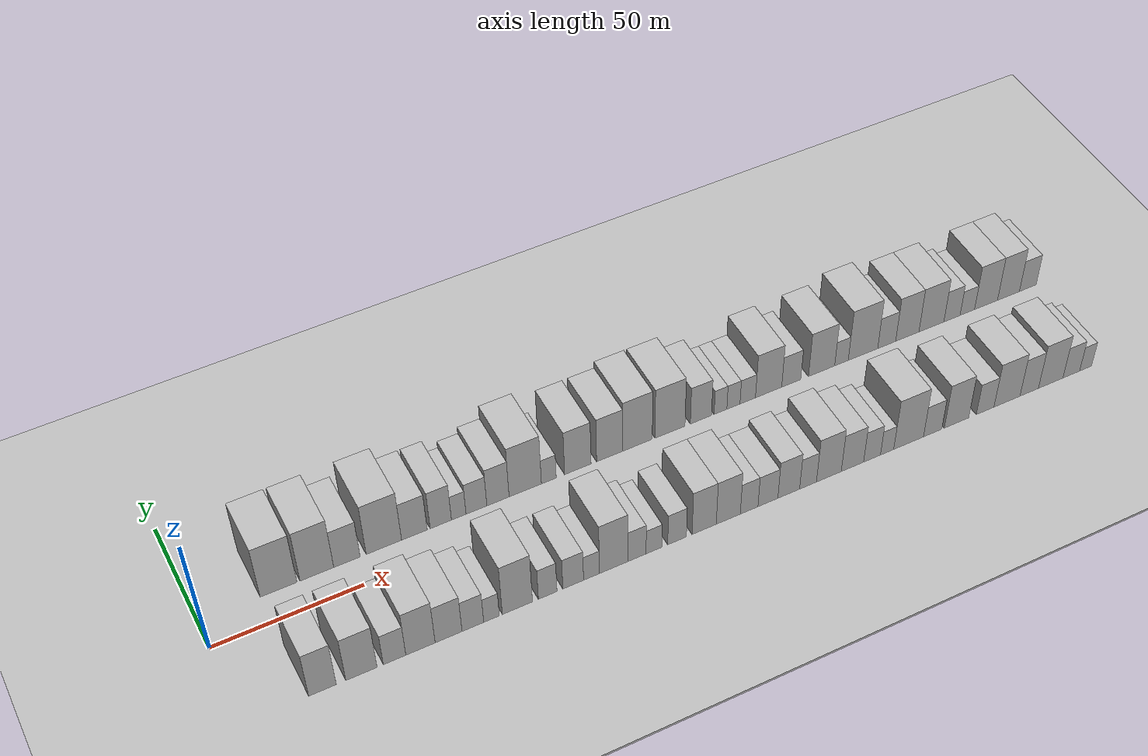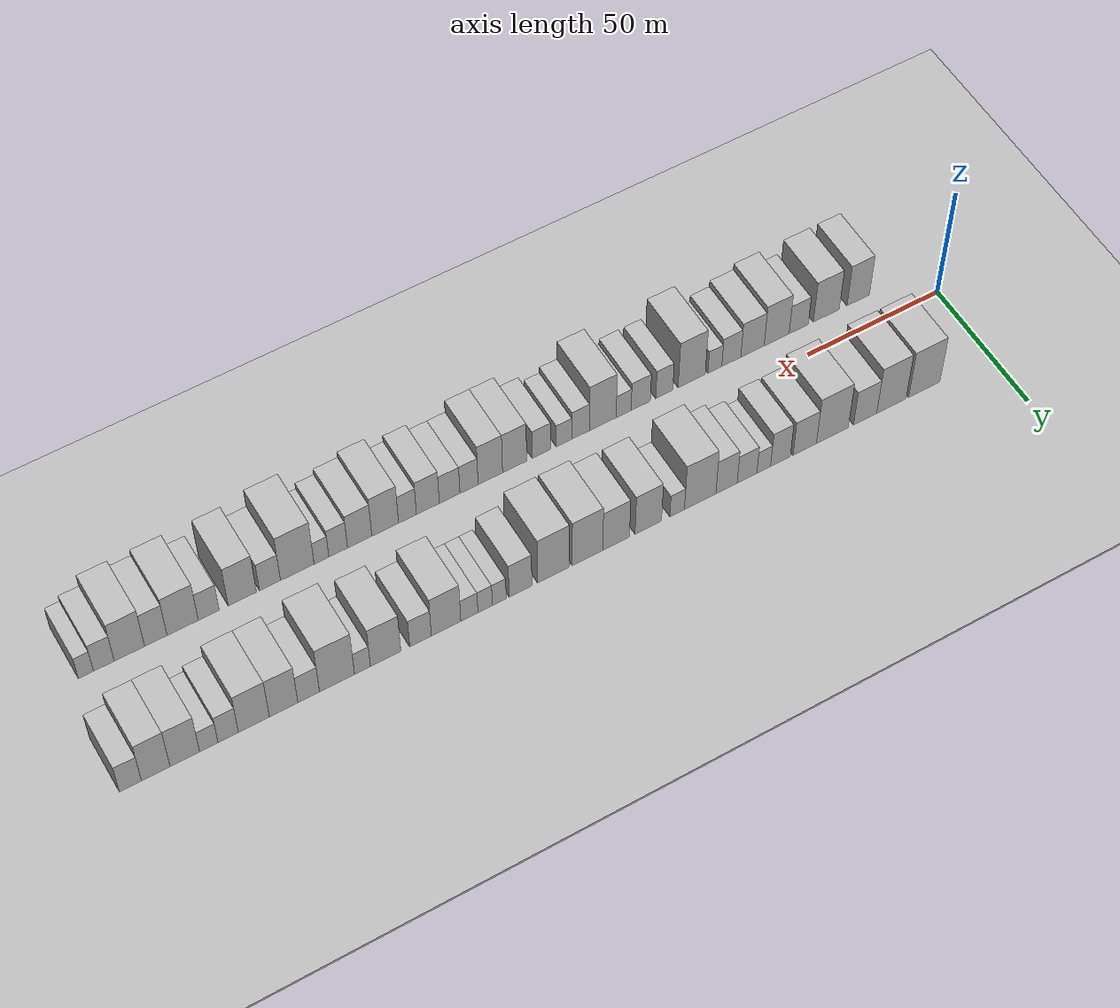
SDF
<?xml version="1.0" encoding="utf-8"?>

<sdf version="1.6">

   <world name="default">

      <gui fullscreen="0">

         <camera name="user_camera">

            <pose>-15 0 4.57585 0 0 0</pose>

            <view_controller>orbit</view_controller>

         </camera>

      </gui>

      <scene>

         <sky>

           <clouds>

             <speed>12</speed>

           </clouds>

         </sky>

         <ambient>0.4 0.4 0.4 1</ambient>

         <background>0.7 0.7 0.7 1</background>

         <shadows>1</shadows>

      </scene>

      <gravity>0 0 -9.8066</gravity>

      <magnetic_field>6e-06 2.3e-05 -4.2e-05</magnetic_field>

      <physics default="0" name="default_physics" type="ode">

         <ode>

            <solver>

               <type>quick</type>

               <iters>10</iters>

               <sor>1.0</sor>

               <use_dynamic_moi_rescaling>0</use_dynamic_moi_rescaling>

            </solver>

            <constraints>

               <cfm>0</cfm>

               <erp>0.2</erp>

               <contact_max_correcting_vel>100</contact_max_correcting_vel>

               <contact_surface_layer>0.001</contact_surface_layer>

            </constraints>

         </ode>

         <max_step_size>0.004</max_step_size>

         <real_time_factor>1</real_time_factor>

         <real_time_update_rate>250</real_time_update_rate>

      </physics>

      <light name="sun" type="directional">

         <cast_shadows>1</cast_shadows>

         <pose>0 0 10 0 0 0</pose>

         <diffuse>0.8 0.8 0.8 1</diffuse>

         <specular>0.2 0.2 0.2 1</specular>

         <attenuation>

            <range>1000</range>

            <constant>0.9</constant>

            <linear>0.01</linear>

            <quadratic>0.001</quadratic>

         </attenuation>

         <direction>-0.5 0.1 -0.9</direction>

      </light>

      <include>

         <name>ground_plane_1</name>

         <uri>model://HANNAS_ground_plane</uri>

         <pose>0 0 0  0 0 0</pose>

      </include>

      <include>

         <name>ground_plane_2</name>

         <uri>model://HANNAS_ground_plane</uri>

         <pose>100 0 0  0 0 0</pose>

      </include>

      <model name="building_1">

         <static>1</static>

         <pose frame="">25.9785 20.0000 0 0.000000 0.000000 1.570796</pose>

         <link name="link">

            <pose frame="">0 0 12.00 0 0 0</pose>

            <collision name="collision">

               <geometry>

                  <box>

                     <size>20.0000 11.9569 24.0000</size>

                  </box>

               </geometry>

               <max_contacts>10</max_contacts>

               <surface>

                  <contact>

                     <ode/>

                  </contact>

                  <bounce/>

                  <friction>

                     <torsional>

                        <ode/>

                     </torsional>

                     <ode/>

                  </friction>

               </surface>

            </collision>

            <visual name="visual">

               <cast_shadows>0</cast_shadows>

               <geometry>

                  <box>

                     <size>20.0000 11.9569 24.0000</size>

                  </box>

               </geometry>

               <material>

                  <script>

                     <uri>model://HANNAS_wall/materials/scripts</uri>

                     <uri>model://HANNAS_wall/materials/textures</uri>

                     <name>vrc/HANNAS_wall</name>

                  </script>

               </material>

            </visual>

            <self_collide>0</self_collide>

            <enable_wind>0</enable_wind>

            <kinematic>0</kinematic>

         </link>

      </model>

      <model name="building_2">

         <static>1</static>

         <pose frame="">38.5101 20.0000 0 0.000000 0.000000 1.570796</pose>

         <link name="link">

            <pose frame="">0 0 12.00 0 0 0</pose>

            <collision name="collision">

               <geometry>

                  <box>

                     <size>20.0000 11.1064 24.0000</size>

                  </box>

               </geometry>

               <max_contacts>10</max_contacts>

               <surface>

                  <contact>

                     <ode/>

                  </contact>

                  <bounce/>

                  <friction>

                     <torsional>

                        <ode/>

                     </torsional>

                     <ode/>

                  </friction>

               </surface>

            </collision>

            <visual name="visual">

               <cast_shadows>0</cast_shadows>

               <geometry>

                  <box>

                     <size>20.0000 11.1064 24.0000</size>

                  </box>

               </geometry>

               <material>

                  <script>

                     <uri>model://HANNAS_wall/materials/scripts</uri>

                     <uri>model://HANNAS_wall/materials/textures</uri>

                     <name>vrc/HANNAS_wall</name>

                  </script>

               </material>

            </visual>

            <self_collide>0</self_collide>

            <enable_wind>0</enable_wind>

            <kinematic>0</kinematic>

         </link>

      </model>

      <model name="building_3">

         <static>1</static>

         <pose frame="">48.4503 20.0000 0 0.000000 0.000000 1.570796</pose>

         <link name="link">

            <pose frame="">0 0 9.00 0 0 0</pose>

            <collision name="collision">

               <geometry>

                  <box>

                     <size>20.0000 8.7741 18.0000</size>

                  </box>

               </geometry>

               <max_contacts>10</max_contacts>

               <surface>

                  <contact>

                     <ode/>

                  </contact>

                  <bounce/>

                  <friction>

                     <torsional>

                        <ode/>

                     </torsional>

                     <ode/>

                  </friction>

               </surface>

            </collision>

            <visual name="visual">

               <cast_shadows>0</cast_shadows>

               <geometry>

                  <box>

                     <size>20.0000 8.7741 18.0000</size>

                  </box>

               </geometry>

               <material>

                  <script>

                     <uri>model://HANNAS_wall/materials/scripts</uri>

                     <uri>model://HANNAS_wall/materials/textures</uri>

                     <name>vrc/HANNAS_wall</name>

                  </script>

               </material>

            </visual>

            <self_collide>0</self_collide>

            <enable_wind>0</enable_wind>

            <kinematic>0</kinematic>

         </link>

      </model>

      <model name="building_4">

         <static>1</static>

         <pose frame="">60.7987 20.0000 0 0.000000 0.000000 1.570796</pose>

         <link name="link">

            <pose frame="">0 0 12.00 0 0 0</pose>

            <collision name="collision">

               <geometry>

                  <box>

                     <size>20.0000 11.9227 24.0000</size>

                  </box>

               </geometry>

               <max_contacts>10</max_contacts>

               <surface>

                  <contact>

                     <ode/>

                  </contact>

                  <bounce/>

                  <friction>

                     <torsional>

                        <ode/>

                     </torsional>

                     <ode/>

                  </friction>

               </surface>

            </collision>

            <visual name="visual">

               <cast_shadows>0</cast_shadows>

               <geometry>

                  <box>

                     <size>20.0000 11.9227 24.0000</size>

                  </box>

               </geometry>

               <material>

                  <script>

                     <uri>model://HANNAS_wall/materials/scripts</uri>

                     <uri>model://HANNAS_wall/materials/textures</uri>

                     <name>vrc/HANNAS_wall</name>

                  </script>

               </material>

            </visual>

            <self_collide>0</self_collide>

            <enable_wind>0</enable_wind>

            <kinematic>0</kinematic>

         </link>

      </model>

      <model name="building_5">

         <static>1</static>

         <pose frame="">71.1130 20.0000 0 0.000000 0.000000 1.570796</pose>

         <link name="link">

            <pose frame="">0 0 9.00 0 0 0</pose>

            <collision name="collision">

               <geometry>

                  <box>

                     <size>20.0000 8.7057 18.0000</size>

                  </box>

               </geometry>

               <max_contacts>10</max_contacts>

               <surface>

                  <contact>

                     <ode/>

                  </contact>

                  <bounce/>

                  <friction>

                     <torsional>

                        <ode/>

                     </torsional>

                     <ode/>

                  </friction>

               </surface>

            </collision>

            <visual name="visual">

               <cast_shadows>0</cast_shadows>

               <geometry>

                  <box>

                     <size>20.0000 8.7057 18.0000</size>

                  </box>

               </geometry>

               <material>

                  <script>

                     <uri>model://HANNAS_wall/materials/scripts</uri>

                     <uri>model://HANNAS_wall/materials/textures</uri>

                     <name>vrc/HANNAS_wall</name>

                  </script>

               </material>

            </visual>

            <self_collide>0</self_collide>

            <enable_wind>0</enable_wind>

            <kinematic>0</kinematic>

         </link>

      </model>

      <model name="building_6">

         <static>1</static>

         <pose frame="">80.1181 20.0000 0 0.000000 0.000000 1.570796</pose>

         <link name="link">

            <pose frame="">0 0 9.00 0 0 0</pose>

            <collision name="collision">

               <geometry>

                  <box>

                     <size>20.0000 7.3044 18.0000</size>

                  </box>

               </geometry>

               <max_contacts>10</max_contacts>

               <surface>

                  <contact>

                     <ode/>

                  </contact>

                  <bounce/>

                  <friction>

                     <torsional>

                        <ode/>

                     </torsional>

                     <ode/>

                  </friction>

               </surface>

            </collision>

            <visual name="visual">

               <cast_shadows>0</cast_shadows>

               <geometry>

                  <box>

                     <size>20.0000 7.3044 18.0000</size>

                  </box>

               </geometry>

               <material>

                  <script>

                     <uri>model://HANNAS_wall/materials/scripts</uri>

                     <uri>model://HANNAS_wall/materials/textures</uri>

                     <name>vrc/HANNAS_wall</name>

                  </script>

               </material>

            </visual>

            <self_collide>0</self_collide>

            <enable_wind>0</enable_wind>

            <kinematic>0</kinematic>

         </link>

      </model>

      <model name="building_7">

         <static>1</static>

         <pose frame="">86.2815 20.0000 0 0.000000 0.000000 1.570796</pose>

         <link name="link">

            <pose frame="">0 0 6.00 0 0 0</pose>

            <collision name="collision">

               <geometry>

                  <box>

                     <size>20.0000 5.0225 12.0000</size>

                  </box>

               </geometry>

               <max_contacts>10</max_contacts>

               <surface>

                  <contact>

                     <ode/>

                  </contact>

                  <bounce/>

                  <friction>

                     <torsional>

                        <ode/>

                     </torsional>

                     <ode/>

                  </friction>

               </surface>

            </collision>

            <visual name="visual">

               <cast_shadows>0</cast_shadows>

               <geometry>

                  <box>

                     <size>20.0000 5.0225 12.0000</size>

                  </box>

               </geometry>

               <material>

                  <script>

                     <uri>model://HANNAS_wall/materials/scripts</uri>

                     <uri>model://HANNAS_wall/materials/textures</uri>

                     <name>vrc/HANNAS_wall</name>

                  </script>

               </material>

            </visual>

            <self_collide>0</self_collide>

            <enable_wind>0</enable_wind>

            <kinematic>0</kinematic>

         </link>

      </model>

      <model name="building_8">

         <static>1</static>

         <pose frame="">92.3983 20.0000 0 0.000000 0.000000 1.570796</pose>

         <link name="link">

            <pose frame="">0 0 7.50 0 0 0</pose>

            <collision name="collision">

               <geometry>

                  <box>

                     <size>20.0000 7.2111 15.0000</size>

                  </box>

               </geometry>

               <max_contacts>10</max_contacts>

               <surface>

                  <contact>

                     <ode/>

                  </contact>

                  <bounce/>

                  <friction>

                     <torsional>

                        <ode/>

                     </torsional>

                     <ode/>

                  </friction>

               </surface>

            </collision>

            <visual name="visual">

               <cast_shadows>0</cast_shadows>

               <geometry>

                  <box>

                     <size>20.0000 7.2111 15.0000</size>

                  </box>

               </geometry>

               <material>

                  <script>

                     <uri>model://HANNAS_wall/materials/scripts</uri>

                     <uri>model://HANNAS_wall/materials/textures</uri>

                     <name>vrc/HANNAS_wall</name>

                  </script>

               </material>

            </visual>

            <self_collide>0</self_collide>

            <enable_wind>0</enable_wind>

            <kinematic>0</kinematic>

         </link>

      </model>

      <model name="building_9">

         <static>1</static>

         <pose frame="">99.8922 20.0000 0 0.000000 0.000000 1.570796</pose>

         <link name="link">

            <pose frame="">0 0 9.00 0 0 0</pose>

            <collision name="collision">

               <geometry>

                  <box>

                     <size>20.0000 7.7767 18.0000</size>

                  </box>

               </geometry>

               <max_contacts>10</max_contacts>

               <surface>

                  <contact>

                     <ode/>

                  </contact>

                  <bounce/>

                  <friction>

                     <torsional>

                        <ode/>

                     </torsional>

                     <ode/>

                  </friction>

               </surface>

            </collision>

            <visual name="visual">

               <cast_shadows>0</cast_shadows>

               <geometry>

                  <box>

                     <size>20.0000 7.7767 18.0000</size>

                  </box>

               </geometry>

               <material>

                  <script>

                     <uri>model://HANNAS_wall/materials/scripts</uri>

                     <uri>model://HANNAS_wall/materials/textures</uri>

                     <name>vrc/HANNAS_wall</name>

                  </script>

               </material>

            </visual>

            <self_collide>0</self_collide>

            <enable_wind>0</enable_wind>

            <kinematic>0</kinematic>

         </link>

      </model>

      <model name="building_10">

         <static>1</static>

         <pose frame="">109.4819 20.0000 0 0.000000 0.000000 1.570796</pose>

         <link name="link">

            <pose frame="">0 0 12.00 0 0 0</pose>

            <collision name="collision">

               <geometry>

                  <box>

                     <size>20.0000 11.4029 24.0000</size>

                  </box>

               </geometry>

               <max_contacts>10</max_contacts>

               <surface>

                  <contact>

                     <ode/>

                  </contact>

                  <bounce/>

                  <friction>

                     <torsional>

                        <ode/>

                     </torsional>

                     <ode/>

                  </friction>

               </surface>

            </collision>

            <visual name="visual">

               <cast_shadows>0</cast_shadows>

               <geometry>

                  <box>

                     <size>20.0000 11.4029 24.0000</size>

                  </box>

               </geometry>

               <material>

                  <script>

                     <uri>model://HANNAS_wall/materials/scripts</uri>

                     <uri>model://HANNAS_wall/materials/textures</uri>

                     <name>vrc/HANNAS_wall</name>

                  </script>

               </material>

            </visual>

            <self_collide>0</self_collide>

            <enable_wind>0</enable_wind>

            <kinematic>0</kinematic>

         </link>

      </model>

      <model name="building_11">

         <static>1</static>

         <pose frame="">117.8091 20.0000 0 0.000000 0.000000 1.570796</pose>

         <link name="link">

            <pose frame="">0 0 6.00 0 0 0</pose>

            <collision name="collision">

               <geometry>

                  <box>

                     <size>20.0000 5.2514 12.0000</size>

                  </box>

               </geometry>

               <max_contacts>10</max_contacts>

               <surface>

                  <contact>

                     <ode/>

                  </contact>

                  <bounce/>

                  <friction>

                     <torsional>

                        <ode/>

                     </torsional>

                     <ode/>

                  </friction>

               </surface>

            </collision>

            <visual name="visual">

               <cast_shadows>0</cast_shadows>

               <geometry>

                  <box>

                     <size>20.0000 5.2514 12.0000</size>

                  </box>

               </geometry>

               <material>

                  <script>

                     <uri>model://HANNAS_wall/materials/scripts</uri>

                     <uri>model://HANNAS_wall/materials/textures</uri>

                     <name>vrc/HANNAS_wall</name>

                  </script>

               </material>

            </visual>

            <self_collide>0</self_collide>

            <enable_wind>0</enable_wind>

            <kinematic>0</kinematic>

         </link>

      </model>

      <model name="building_12">

         <static>1</static>

         <pose frame="">128.1801 20.0000 0 0.000000 0.000000 1.570796</pose>

         <link name="link">

            <pose frame="">0 0 10.50 0 0 0</pose>

            <collision name="collision">

               <geometry>

                  <box>

                     <size>20.0000 9.4906 21.0000</size>

                  </box>

               </geometry>

               <max_contacts>10</max_contacts>

               <surface>

                  <contact>

                     <ode/>

                  </contact>

                  <bounce/>

                  <friction>

                     <torsional>

                        <ode/>

                     </torsional>

                     <ode/>

                  </friction>

               </surface>

            </collision>

            <visual name="visual">

               <cast_shadows>0</cast_shadows>

               <geometry>

                  <box>

                     <size>20.0000 9.4906 21.0000</size>

                  </box>

               </geometry>

               <material>

                  <script>

                     <uri>model://HANNAS_wall/materials/scripts</uri>

                     <uri>model://HANNAS_wall/materials/textures</uri>

                     <name>vrc/HANNAS_wall</name>

                  </script>

               </material>

            </visual>

            <self_collide>0</self_collide>

            <enable_wind>0</enable_wind>

            <kinematic>0</kinematic>

         </link>

      </model>

      <model name="building_13">

         <static>1</static>

         <pose frame="">139.6818 20.0000 0 0.000000 0.000000 1.570796</pose>

         <link name="link">

            <pose frame="">0 0 10.50 0 0 0</pose>

            <collision name="collision">

               <geometry>

                  <box>

                     <size>20.0000 9.5127 21.0000</size>

                  </box>

               </geometry>

               <max_contacts>10</max_contacts>

               <surface>

                  <contact>

                     <ode/>

                  </contact>

                  <bounce/>

                  <friction>

                     <torsional>

                        <ode/>

                     </torsional>

                     <ode/>

                  </friction>

               </surface>

            </collision>

            <visual name="visual">

               <cast_shadows>0</cast_shadows>

               <geometry>

                  <box>

                     <size>20.0000 9.5127 21.0000</size>

                  </box>

               </geometry>

               <material>

                  <script>

                     <uri>model://HANNAS_wall/materials/scripts</uri>

                     <uri>model://HANNAS_wall/materials/textures</uri>

                     <name>vrc/HANNAS_wall</name>

                  </script>

               </material>

            </visual>

            <self_collide>0</self_collide>

            <enable_wind>0</enable_wind>

            <kinematic>0</kinematic>

         </link>

      </model>

      <model name="building_14">

         <static>1</static>

         <pose frame="">149.8260 20.0000 0 0.000000 0.000000 1.570796</pose>

         <link name="link">

            <pose frame="">0 0 12.00 0 0 0</pose>

            <collision name="collision">

               <geometry>

                  <box>

                     <size>20.0000 10.7758 24.0000</size>

                  </box>

               </geometry>

               <max_contacts>10</max_contacts>

               <surface>

                  <contact>

                     <ode/>

                  </contact>

                  <bounce/>

                  <friction>

                     <torsional>

                        <ode/>

                     </torsional>

                     <ode/>

                  </friction>

               </surface>

            </collision>

            <visual name="visual">

               <cast_shadows>0</cast_shadows>

               <geometry>

                  <box>

                     <size>20.0000 10.7758 24.0000</size>

                  </box>

               </geometry>

               <material>

                  <script>

                     <uri>model://HANNAS_wall/materials/scripts</uri>

                     <uri>model://HANNAS_wall/materials/textures</uri>

                     <name>vrc/HANNAS_wall</name>

                  </script>

               </material>

            </visual>

            <self_collide>0</self_collide>

            <enable_wind>0</enable_wind>

            <kinematic>0</kinematic>

         </link>

      </model>

      <model name="building_15">

         <static>1</static>

         <pose frame="">161.7693 20.0000 0 0.000000 0.000000 1.570796</pose>

         <link name="link">

            <pose frame="">0 0 12.00 0 0 0</pose>

            <collision name="collision">

               <geometry>

                  <box>

                     <size>20.0000 11.1109 24.0000</size>

                  </box>

               </geometry>

               <max_contacts>10</max_contacts>

               <surface>

                  <contact>

                     <ode/>

                  </contact>

                  <bounce/>

                  <friction>

                     <torsional>

                        <ode/>

                     </torsional>

                     <ode/>

                  </friction>

               </surface>

            </collision>

            <visual name="visual">

               <cast_shadows>0</cast_shadows>

               <geometry>

                  <box>

                     <size>20.0000 11.1109 24.0000</size>

                  </box>

               </geometry>

               <material>

                  <script>

                     <uri>model://HANNAS_wall/materials/scripts</uri>

                     <uri>model://HANNAS_wall/materials/textures</uri>

                     <name>vrc/HANNAS_wall</name>

                  </script>

               </material>

            </visual>

            <self_collide>0</self_collide>

            <enable_wind>0</enable_wind>

            <kinematic>0</kinematic>

         </link>

      </model>

      <model name="building_16">

         <static>1</static>

         <pose frame="">173.2774 20.0000 0 0.000000 0.000000 1.570796</pose>

         <link name="link">

            <pose frame="">0 0 9.00 0 0 0</pose>

            <collision name="collision">

               <geometry>

                  <box>

                     <size>20.0000 7.9053 18.0000</size>

                  </box>

               </geometry>

               <max_contacts>10</max_contacts>

               <surface>

                  <contact>

                     <ode/>

                  </contact>

                  <bounce/>

                  <friction>

                     <torsional>

                        <ode/>

                     </torsional>

                     <ode/>

                  </friction>

               </surface>

            </collision>

            <visual name="visual">

               <cast_shadows>0</cast_shadows>

               <geometry>

                  <box>

                     <size>20.0000 7.9053 18.0000</size>

                  </box>

               </geometry>

               <material>

                  <script>

                     <uri>model://HANNAS_wall/materials/scripts</uri>

                     <uri>model://HANNAS_wall/materials/textures</uri>

                     <name>vrc/HANNAS_wall</name>

                  </script>

               </material>

            </visual>

            <self_collide>0</self_collide>

            <enable_wind>0</enable_wind>

            <kinematic>0</kinematic>

         </link>

      </model>

      <model name="building_17">

         <static>1</static>

         <pose frame="">180.6325 20.0000 0 0.000000 0.000000 1.570796</pose>

         <link name="link">

            <pose frame="">0 0 6.00 0 0 0</pose>

            <collision name="collision">

               <geometry>

                  <box>

                     <size>20.0000 4.8050 12.0000</size>

                  </box>

               </geometry>

               <max_contacts>10</max_contacts>

               <surface>

                  <contact>

                     <ode/>

                  </contact>

                  <bounce/>

                  <friction>

                     <torsional>

                        <ode/>

                     </torsional>

                     <ode/>

                  </friction>

               </surface>

            </collision>

            <visual name="visual">

               <cast_shadows>0</cast_shadows>

               <geometry>

                  <box>

                     <size>20.0000 4.8050 12.0000</size>

                  </box>

               </geometry>

               <material>

                  <script>

                     <uri>model://HANNAS_wall/materials/scripts</uri>

                     <uri>model://HANNAS_wall/materials/textures</uri>

                     <name>vrc/HANNAS_wall</name>

                  </script>

               </material>

            </visual>

            <self_collide>0</self_collide>

            <enable_wind>0</enable_wind>

            <kinematic>0</kinematic>

         </link>

      </model>

      <model name="building_18">

         <static>1</static>

         <pose frame="">185.5237 20.0000 0 0.000000 0.000000 1.570796</pose>

         <link name="link">

            <pose frame="">0 0 6.00 0 0 0</pose>

            <collision name="collision">

               <geometry>

                  <box>

                     <size>20.0000 4.9772 12.0000</size>

                  </box>

               </geometry>

               <max_contacts>10</max_contacts>

               <surface>

                  <contact>

                     <ode/>

                  </contact>

                  <bounce/>

                  <friction>

                     <torsional>

                        <ode/>

                     </torsional>

                     <ode/>

                  </friction>

               </surface>

            </collision>

            <visual name="visual">

               <cast_shadows>0</cast_shadows>

               <geometry>

                  <box>

                     <size>20.0000 4.9772 12.0000</size>

                  </box>

               </geometry>

               <material>

                  <script>

                     <uri>model://HANNAS_wall/materials/scripts</uri>

                     <uri>model://HANNAS_wall/materials/textures</uri>

                     <name>vrc/HANNAS_wall</name>

                  </script>

               </material>

            </visual>

            <self_collide>0</self_collide>

            <enable_wind>0</enable_wind>

            <kinematic>0</kinematic>

         </link>

      </model>

      <model name="building_19">

         <static>1</static>

         <pose frame="">190.9537 20.0000 0 0.000000 0.000000 1.570796</pose>

         <link name="link">

            <pose frame="">0 0 6.00 0 0 0</pose>

            <collision name="collision">

               <geometry>

                  <box>

                     <size>20.0000 5.8828 12.0000</size>

                  </box>

               </geometry>

               <max_contacts>10</max_contacts>

               <surface>

                  <contact>

                     <ode/>

                  </contact>

                  <bounce/>

                  <friction>

                     <torsional>

                        <ode/>

                     </torsional>

                     <ode/>

                  </friction>

               </surface>

            </collision>

            <visual name="visual">

               <cast_shadows>0</cast_shadows>

               <geometry>

                  <box>

                     <size>20.0000 5.8828 12.0000</size>

                  </box>

               </geometry>

               <material>

                  <script>

                     <uri>model://HANNAS_wall/materials/scripts</uri>

                     <uri>model://HANNAS_wall/materials/textures</uri>

                     <name>vrc/HANNAS_wall</name>

                  </script>

               </material>

            </visual>

            <self_collide>0</self_collide>

            <enable_wind>0</enable_wind>

            <kinematic>0</kinematic>

         </link>

      </model>

      <model name="building_20">

         <static>1</static>

         <pose frame="">198.9248 20.0000 0 0.000000 0.000000 1.570796</pose>

         <link name="link">

            <pose frame="">0 0 10.50 0 0 0</pose>

            <collision name="collision">

               <geometry>

                  <box>

                     <size>20.0000 10.0593 21.0000</size>

                  </box>

               </geometry>

               <max_contacts>10</max_contacts>

               <surface>

                  <contact>

                     <ode/>

                  </contact>

                  <bounce/>

                  <friction>

                     <torsional>

                        <ode/>

                     </torsional>

                     <ode/>

                  </friction>

               </surface>

            </collision>

            <visual name="visual">

               <cast_shadows>0</cast_shadows>

               <geometry>

                  <box>

                     <size>20.0000 10.0593 21.0000</size>

                  </box>

               </geometry>

               <material>

                  <script>

                     <uri>model://HANNAS_wall/materials/scripts</uri>

                     <uri>model://HANNAS_wall/materials/textures</uri>

                     <name>vrc/HANNAS_wall</name>

                  </script>

               </material>

            </visual>

            <self_collide>0</self_collide>

            <enable_wind>0</enable_wind>

            <kinematic>0</kinematic>

         </link>

      </model>

      <model name="building_21">

         <static>1</static>

         <pose frame="">207.6356 20.0000 0 0.000000 0.000000 1.570796</pose>

         <link name="link">

            <pose frame="">0 0 7.50 0 0 0</pose>

            <collision name="collision">

               <geometry>

                  <box>

                     <size>20.0000 7.3625 15.0000</size>

                  </box>

               </geometry>

               <max_contacts>10</max_contacts>

               <surface>

                  <contact>

                     <ode/>

                  </contact>

                  <bounce/>

                  <friction>

                     <torsional>

                        <ode/>

                     </torsional>

                     <ode/>

                  </friction>

               </surface>

            </collision>

            <visual name="visual">

               <cast_shadows>0</cast_shadows>

               <geometry>

                  <box>

                     <size>20.0000 7.3625 15.0000</size>

                  </box>

               </geometry>

               <material>

                  <script>

                     <uri>model://HANNAS_wall/materials/scripts</uri>

                     <uri>model://HANNAS_wall/materials/textures</uri>

                     <name>vrc/HANNAS_wall</name>

                  </script>

               </material>

            </visual>

            <self_collide>0</self_collide>

            <enable_wind>0</enable_wind>

            <kinematic>0</kinematic>

         </link>

      </model>

      <model name="building_22">

         <static>1</static>

         <pose frame="">219.4383 20.0000 0 0.000000 0.000000 1.570796</pose>

         <link name="link">

            <pose frame="">0 0 10.50 0 0 0</pose>

            <collision name="collision">

               <geometry>

                  <box>

                     <size>20.0000 10.2429 21.0000</size>

                  </box>

               </geometry>

               <max_contacts>10</max_contacts>

               <surface>

                  <contact>

                     <ode/>

                  </contact>

                  <bounce/>

                  <friction>

                     <torsional>

                        <ode/>

                     </torsional>

                     <ode/>

                  </friction>

               </surface>

            </collision>

            <visual name="visual">

               <cast_shadows>0</cast_shadows>

               <geometry>

                  <box>

                     <size>20.0000 10.2429 21.0000</size>

                  </box>

               </geometry>

               <material>

                  <script>

                     <uri>model://HANNAS_wall/materials/scripts</uri>

                     <uri>model://HANNAS_wall/materials/textures</uri>

                     <name>vrc/HANNAS_wall</name>

                  </script>

               </material>

            </visual>

            <self_collide>0</self_collide>

            <enable_wind>0</enable_wind>

            <kinematic>0</kinematic>

         </link>

      </model>

      <model name="building_23">

         <static>1</static>

         <pose frame="">227.2261 20.0000 0 0.000000 0.000000 1.570796</pose>

         <link name="link">

            <pose frame="">0 0 6.00 0 0 0</pose>

            <collision name="collision">

               <geometry>

                  <box>

                     <size>20.0000 5.3326 12.0000</size>

                  </box>

               </geometry>

               <max_contacts>10</max_contacts>

               <surface>

                  <contact>

                     <ode/>

                  </contact>

                  <bounce/>

                  <friction>

                     <torsional>

                        <ode/>

                     </torsional>

                     <ode/>

                  </friction>

               </surface>

            </collision>

            <visual name="visual">

               <cast_shadows>0</cast_shadows>

               <geometry>

                  <box>

                     <size>20.0000 5.3326 12.0000</size>

                  </box>

               </geometry>

               <material>

                  <script>

                     <uri>model://HANNAS_wall/materials/scripts</uri>

                     <uri>model://HANNAS_wall/materials/textures</uri>

                     <name>vrc/HANNAS_wall</name>

                  </script>

               </material>

            </visual>

            <self_collide>0</self_collide>

            <enable_wind>0</enable_wind>

            <kinematic>0</kinematic>

         </link>

      </model>

      <model name="building_24">

         <static>1</static>

         <pose frame="">235.7231 20.0000 0 0.000000 0.000000 1.570796</pose>

         <link name="link">

            <pose frame="">0 0 12.00 0 0 0</pose>

            <collision name="collision">

               <geometry>

                  <box>

                     <size>20.0000 11.6614 24.0000</size>

                  </box>

               </geometry>

               <max_contacts>10</max_contacts>

               <surface>

                  <contact>

                     <ode/>

                  </contact>

                  <bounce/>

                  <friction>

                     <torsional>

                        <ode/>

                     </torsional>

                     <ode/>

                  </friction>

               </surface>

            </collision>

            <visual name="visual">

               <cast_shadows>0</cast_shadows>

               <geometry>

                  <box>

                     <size>20.0000 11.6614 24.0000</size>

                  </box>

               </geometry>

               <material>

                  <script>

                     <uri>model://HANNAS_wall/materials/scripts</uri>

                     <uri>model://HANNAS_wall/materials/textures</uri>

                     <name>vrc/HANNAS_wall</name>

                  </script>

               </material>

            </visual>

            <self_collide>0</self_collide>

            <enable_wind>0</enable_wind>

            <kinematic>0</kinematic>

         </link>

      </model>

      <model name="building_25">

         <static>1</static>

         <pose frame="">245.1435 20.0000 0 0.000000 0.000000 1.570796</pose>

         <link name="link">

            <pose frame="">0 0 7.50 0 0 0</pose>

            <collision name="collision">

               <geometry>

                  <box>

                     <size>20.0000 7.1794 15.0000</size>

                  </box>

               </geometry>

               <max_contacts>10</max_contacts>

               <surface>

                  <contact>

                     <ode/>

                  </contact>

                  <bounce/>

                  <friction>

                     <torsional>

                        <ode/>

                     </torsional>

                     <ode/>

                  </friction>

               </surface>

            </collision>

            <visual name="visual">

               <cast_shadows>0</cast_shadows>

               <geometry>

                  <box>

                     <size>20.0000 7.1794 15.0000</size>

                  </box>

               </geometry>

               <material>

                  <script>

                     <uri>model://HANNAS_wall/materials/scripts</uri>

                     <uri>model://HANNAS_wall/materials/textures</uri>

                     <name>vrc/HANNAS_wall</name>

                  </script>

               </material>

            </visual>

            <self_collide>0</self_collide>

            <enable_wind>0</enable_wind>

            <kinematic>0</kinematic>

         </link>

      </model>

      <model name="building_26">

         <static>1</static>

         <pose frame="">253.4254 20.0000 0 0.000000 0.000000 1.570796</pose>

         <link name="link">

            <pose frame="">0 0 10.50 0 0 0</pose>

            <collision name="collision">

               <geometry>

                  <box>

                     <size>20.0000 9.3844 21.0000</size>

                  </box>

               </geometry>

               <max_contacts>10</max_contacts>

               <surface>

                  <contact>

                     <ode/>

                  </contact>

                  <bounce/>

                  <friction>

                     <torsional>

                        <ode/>

                     </torsional>

                     <ode/>

                  </friction>

               </surface>

            </collision>

            <visual name="visual">

               <cast_shadows>0</cast_shadows>

               <geometry>

                  <box>

                     <size>20.0000 9.3844 21.0000</size>

                  </box>

               </geometry>

               <material>

                  <script>

                     <uri>model://HANNAS_wall/materials/scripts</uri>

                     <uri>model://HANNAS_wall/materials/textures</uri>

                     <name>vrc/HANNAS_wall</name>

                  </script>

               </material>

            </visual>

            <self_collide>0</self_collide>

            <enable_wind>0</enable_wind>

            <kinematic>0</kinematic>

         </link>

      </model>

      <model name="building_27">

         <static>1</static>

         <pose frame="">263.1952 20.0000 0 0.000000 0.000000 1.570796</pose>

         <link name="link">

            <pose frame="">0 0 10.50 0 0 0</pose>

            <collision name="collision">

               <geometry>

                  <box>

                     <size>20.0000 10.1553 21.0000</size>

                  </box>

               </geometry>

               <max_contacts>10</max_contacts>

               <surface>

                  <contact>

                     <ode/>

                  </contact>

                  <bounce/>

                  <friction>

                     <torsional>

                        <ode/>

                     </torsional>

                     <ode/>

                  </friction>

               </surface>

            </collision>

            <visual name="visual">

               <cast_shadows>0</cast_shadows>

               <geometry>

                  <box>

                     <size>20.0000 10.1553 21.0000</size>

                  </box>

               </geometry>

               <material>

                  <script>

                     <uri>model://HANNAS_wall/materials/scripts</uri>

                     <uri>model://HANNAS_wall/materials/textures</uri>

                     <name>vrc/HANNAS_wall</name>

                  </script>

               </material>

            </visual>

            <self_collide>0</self_collide>

            <enable_wind>0</enable_wind>

            <kinematic>0</kinematic>

         </link>

      </model>

      <model name="building_28">

         <static>1</static>

         <pose frame="">271.5869 20.0000 0 0.000000 0.000000 1.570796</pose>

         <link name="link">

            <pose frame="">0 0 7.50 0 0 0</pose>

            <collision name="collision">

               <geometry>

                  <box>

                     <size>20.0000 6.6281 15.0000</size>

                  </box>

               </geometry>

               <max_contacts>10</max_contacts>

               <surface>

                  <contact>

                     <ode/>

                  </contact>

                  <bounce/>

                  <friction>

                     <torsional>

                        <ode/>

                     </torsional>

                     <ode/>

                  </friction>

               </surface>

            </collision>

            <visual name="visual">

               <cast_shadows>0</cast_shadows>

               <geometry>

                  <box>

                     <size>20.0000 6.6281 15.0000</size>

                  </box>

               </geometry>

               <material>

                  <script>

                     <uri>model://HANNAS_wall/materials/scripts</uri>

                     <uri>model://HANNAS_wall/materials/textures</uri>

                     <name>vrc/HANNAS_wall</name>

                  </script>

               </material>

            </visual>

            <self_collide>0</self_collide>

            <enable_wind>0</enable_wind>

            <kinematic>0</kinematic>

         </link>

      </model>

      <model name="building_29">

         <static>1</static>

         <pose frame="">277.8833 20.0000 0 0.000000 0.000000 1.570796</pose>

         <link name="link">

            <pose frame="">0 0 6.00 0 0 0</pose>

            <collision name="collision">

               <geometry>

                  <box>

                     <size>20.0000 5.9647 12.0000</size>

                  </box>

               </geometry>

               <max_contacts>10</max_contacts>

               <surface>

                  <contact>

                     <ode/>

                  </contact>

                  <bounce/>

                  <friction>

                     <torsional>

                        <ode/>

                     </torsional>

                     <ode/>

                  </friction>

               </surface>

            </collision>

            <visual name="visual">

               <cast_shadows>0</cast_shadows>

               <geometry>

                  <box>

                     <size>20.0000 5.9647 12.0000</size>

                  </box>

               </geometry>

               <material>

                  <script>

                     <uri>model://HANNAS_wall/materials/scripts</uri>

                     <uri>model://HANNAS_wall/materials/textures</uri>

                     <name>vrc/HANNAS_wall</name>

                  </script>

               </material>

            </visual>

            <self_collide>0</self_collide>

            <enable_wind>0</enable_wind>

            <kinematic>0</kinematic>

         </link>

      </model>

      <model name="building_30">

         <static>1</static>

         <pose frame="">285.6277 20.0000 0 0.000000 0.000000 1.570796</pose>

         <link name="link">

            <pose frame="">0 0 10.50 0 0 0</pose>

            <collision name="collision">

               <geometry>

                  <box>

                     <size>20.0000 9.5241 21.0000</size>

                  </box>

               </geometry>

               <max_contacts>10</max_contacts>

               <surface>

                  <contact>

                     <ode/>

                  </contact>

                  <bounce/>

                  <friction>

                     <torsional>

                        <ode/>

                     </torsional>

                     <ode/>

                  </friction>

               </surface>

            </collision>

            <visual name="visual">

               <cast_shadows>0</cast_shadows>

               <geometry>

                  <box>

                     <size>20.0000 9.5241 21.0000</size>

                  </box>

               </geometry>

               <material>

                  <script>

                     <uri>model://HANNAS_wall/materials/scripts</uri>

                     <uri>model://HANNAS_wall/materials/textures</uri>

                     <name>vrc/HANNAS_wall</name>

                  </script>

               </material>

            </visual>

            <self_collide>0</self_collide>

            <enable_wind>0</enable_wind>

            <kinematic>0</kinematic>

         </link>

      </model>

      <model name="building_31">

         <static>1</static>

         <pose frame="">294.9660 20.0000 0 0.000000 0.000000 1.570796</pose>

         <link name="link">

            <pose frame="">0 0 10.50 0 0 0</pose>

            <collision name="collision">

               <geometry>

                  <box>

                     <size>20.0000 9.1525 21.0000</size>

                  </box>

               </geometry>

               <max_contacts>10</max_contacts>

               <surface>

                  <contact>

                     <ode/>

                  </contact>

                  <bounce/>

                  <friction>

                     <torsional>

                        <ode/>

                     </torsional>

                     <ode/>

                  </friction>

               </surface>

            </collision>

            <visual name="visual">

               <cast_shadows>0</cast_shadows>

               <geometry>

                  <box>

                     <size>20.0000 9.1525 21.0000</size>

                  </box>

               </geometry>

               <material>

                  <script>

                     <uri>model://HANNAS_wall/materials/scripts</uri>

                     <uri>model://HANNAS_wall/materials/textures</uri>

                     <name>vrc/HANNAS_wall</name>

                  </script>

               </material>

            </visual>

            <self_collide>0</self_collide>

            <enable_wind>0</enable_wind>

            <kinematic>0</kinematic>

         </link>

      </model>

      <model name="building_32">

         <static>1</static>

         <pose frame="">303.0632 20.0000 0 0.000000 0.000000 1.570796</pose>

         <link name="link">

            <pose frame="">0 0 7.50 0 0 0</pose>

            <collision name="collision">

               <geometry>

                  <box>

                     <size>20.0000 7.0419 15.0000</size>

                  </box>

               </geometry>

               <max_contacts>10</max_contacts>

               <surface>

                  <contact>

                     <ode/>

                  </contact>

                  <bounce/>

                  <friction>

                     <torsional>

                        <ode/>

                     </torsional>

                     <ode/>

                  </friction>

               </surface>

            </collision>

            <visual name="visual">

               <cast_shadows>0</cast_shadows>

               <geometry>

                  <box>

                     <size>20.0000 7.0419 15.0000</size>

                  </box>

               </geometry>

               <material>

                  <script>

                     <uri>model://HANNAS_wall/materials/scripts</uri>

                     <uri>model://HANNAS_wall/materials/textures</uri>

                     <name>vrc/HANNAS_wall</name>

                  </script>

               </material>

            </visual>

            <self_collide>0</self_collide>

            <enable_wind>0</enable_wind>

            <kinematic>0</kinematic>

         </link>

      </model>

      <model name="building_33">

         <static>1</static>

         <pose frame="">24.3545 -20.0000 0 0.000000 0.000000 1.570796</pose>

         <link name="link">

            <pose frame="">0 0 10.50 0 0 0</pose>

            <collision name="collision">

               <geometry>

                  <box>

                     <size>20.0000 8.7090 21.0000</size>

                  </box>

               </geometry>

               <max_contacts>10</max_contacts>

               <surface>

                  <contact>

                     <ode/>

                  </contact>

                  <bounce/>

                  <friction>

                     <torsional>

                        <ode/>

                     </torsional>

                     <ode/>

                  </friction>

               </surface>

            </collision>

            <visual name="visual">

               <cast_shadows>0</cast_shadows>

               <geometry>

                  <box>

                     <size>20.0000 8.7090 21.0000</size>

                  </box>

               </geometry>

               <material>

                  <script>

                     <uri>model://HANNAS_wall/materials/scripts</uri>

                     <uri>model://HANNAS_wall/materials/textures</uri>

                     <name>vrc/HANNAS_wall</name>

                  </script>

               </material>

            </visual>

            <self_collide>0</self_collide>

            <enable_wind>0</enable_wind>

            <kinematic>0</kinematic>

         </link>

      </model>

      <model name="building_34">

         <static>1</static>

         <pose frame="">36.6917 -20.0000 0 0.000000 0.000000 1.570796</pose>

         <link name="link">

            <pose frame="">0 0 10.50 0 0 0</pose>

            <collision name="collision">

               <geometry>

                  <box>

                     <size>20.0000 9.9654 21.0000</size>

                  </box>

               </geometry>

               <max_contacts>10</max_contacts>

               <surface>

                  <contact>

                     <ode/>

                  </contact>

                  <bounce/>

                  <friction>

                     <torsional>

                        <ode/>

                     </torsional>

                     <ode/>

                  </friction>

               </surface>

            </collision>

            <visual name="visual">

               <cast_shadows>0</cast_shadows>

               <geometry>

                  <box>

                     <size>20.0000 9.9654 21.0000</size>

                  </box>

               </geometry>

               <material>

                  <script>

                     <uri>model://HANNAS_wall/materials/scripts</uri>

                     <uri>model://HANNAS_wall/materials/textures</uri>

                     <name>vrc/HANNAS_wall</name>

                  </script>

               </material>

            </visual>

            <self_collide>0</self_collide>

            <enable_wind>0</enable_wind>

            <kinematic>0</kinematic>

         </link>

      </model>

      <model name="building_35">

         <static>1</static>

         <pose frame="">47.3037 -20.0000 0 0.000000 0.000000 1.570796</pose>

         <link name="link">

            <pose frame="">0 0 7.50 0 0 0</pose>

            <collision name="collision">

               <geometry>

                  <box>

                     <size>20.0000 7.2587 15.0000</size>

                  </box>

               </geometry>

               <max_contacts>10</max_contacts>

               <surface>

                  <contact>

                     <ode/>

                  </contact>

                  <bounce/>

                  <friction>

                     <torsional>

                        <ode/>

                     </torsional>

                     <ode/>

                  </friction>

               </surface>

            </collision>

            <visual name="visual">

               <cast_shadows>0</cast_shadows>

               <geometry>

                  <box>

                     <size>20.0000 7.2587 15.0000</size>

                  </box>

               </geometry>

               <material>

                  <script>

                     <uri>model://HANNAS_wall/materials/scripts</uri>

                     <uri>model://HANNAS_wall/materials/textures</uri>

                     <name>vrc/HANNAS_wall</name>

                  </script>

               </material>

            </visual>

            <self_collide>0</self_collide>

            <enable_wind>0</enable_wind>

            <kinematic>0</kinematic>

         </link>

      </model>

      <model name="building_36">

         <static>1</static>

         <pose frame="">55.6943 -20.0000 0 0.000000 0.000000 1.570796</pose>

         <link name="link">

            <pose frame="">0 0 10.50 0 0 0</pose>

            <collision name="collision">

               <geometry>

                  <box>

                     <size>20.0000 9.5226 21.0000</size>

                  </box>

               </geometry>

               <max_contacts>10</max_contacts>

               <surface>

                  <contact>

                     <ode/>

                  </contact>

                  <bounce/>

                  <friction>

                     <torsional>

                        <ode/>

                     </torsional>

                     <ode/>

                  </friction>

               </surface>

            </collision>

            <visual name="visual">

               <cast_shadows>0</cast_shadows>

               <geometry>

                  <box>

                     <size>20.0000 9.5226 21.0000</size>

                  </box>

               </geometry>

               <material>

                  <script>

                     <uri>model://HANNAS_wall/materials/scripts</uri>

                     <uri>model://HANNAS_wall/materials/textures</uri>

                     <name>vrc/HANNAS_wall</name>

                  </script>

               </material>

            </visual>

            <self_collide>0</self_collide>

            <enable_wind>0</enable_wind>

            <kinematic>0</kinematic>

         </link>

      </model>

      <model name="building_37">

         <static>1</static>

         <pose frame="">64.8695 -20.0000 0 0.000000 0.000000 1.570796</pose>

         <link name="link">

            <pose frame="">0 0 9.00 0 0 0</pose>

            <collision name="collision">

               <geometry>

                  <box>

                     <size>20.0000 8.8278 18.0000</size>

                  </box>

               </geometry>

               <max_contacts>10</max_contacts>

               <surface>

                  <contact>

                     <ode/>

                  </contact>

                  <bounce/>

                  <friction>

                     <torsional>

                        <ode/>

                     </torsional>

                     <ode/>

                  </friction>

               </surface>

            </collision>

            <visual name="visual">

               <cast_shadows>0</cast_shadows>

               <geometry>

                  <box>

                     <size>20.0000 8.8278 18.0000</size>

                  </box>

               </geometry>

               <material>

                  <script>

                     <uri>model://HANNAS_wall/materials/scripts</uri>

                     <uri>model://HANNAS_wall/materials/textures</uri>

                     <name>vrc/HANNAS_wall</name>

                  </script>

               </material>

            </visual>

            <self_collide>0</self_collide>

            <enable_wind>0</enable_wind>

            <kinematic>0</kinematic>

         </link>

      </model>

      <model name="building_38">

         <static>1</static>

         <pose frame="">72.8597 -20.0000 0 0.000000 0.000000 1.570796</pose>

         <link name="link">

            <pose frame="">0 0 7.50 0 0 0</pose>

            <collision name="collision">

               <geometry>

                  <box>

                     <size>20.0000 7.1525 15.0000</size>

                  </box>

               </geometry>

               <max_contacts>10</max_contacts>

               <surface>

                  <contact>

                     <ode/>

                  </contact>

                  <bounce/>

                  <friction>

                     <torsional>

                        <ode/>

                     </torsional>

                     <ode/>

                  </friction>

               </surface>

            </collision>

            <visual name="visual">

               <cast_shadows>0</cast_shadows>

               <geometry>

                  <box>

                     <size>20.0000 7.1525 15.0000</size>

                  </box>

               </geometry>

               <material>

                  <script>

                     <uri>model://HANNAS_wall/materials/scripts</uri>

                     <uri>model://HANNAS_wall/materials/textures</uri>

                     <name>vrc/HANNAS_wall</name>

                  </script>

               </material>

            </visual>

            <self_collide>0</self_collide>

            <enable_wind>0</enable_wind>

            <kinematic>0</kinematic>

         </link>

      </model>

      <model name="building_39">

         <static>1</static>

         <pose frame="">79.0361 -20.0000 0 0.000000 0.000000 1.570796</pose>

         <link name="link">

            <pose frame="">0 0 6.00 0 0 0</pose>

            <collision name="collision">

               <geometry>

                  <box>

                     <size>20.0000 5.2004 12.0000</size>

                  </box>

               </geometry>

               <max_contacts>10</max_contacts>

               <surface>

                  <contact>

                     <ode/>

                  </contact>

                  <bounce/>

                  <friction>

                     <torsional>

                        <ode/>

                     </torsional>

                     <ode/>

                  </friction>

               </surface>

            </collision>

            <visual name="visual">

               <cast_shadows>0</cast_shadows>

               <geometry>

                  <box>

                     <size>20.0000 5.2004 12.0000</size>

                  </box>

               </geometry>

               <material>

                  <script>

                     <uri>model://HANNAS_wall/materials/scripts</uri>

                     <uri>model://HANNAS_wall/materials/textures</uri>

                     <name>vrc/HANNAS_wall</name>

                  </script>

               </material>

            </visual>

            <self_collide>0</self_collide>

            <enable_wind>0</enable_wind>

            <kinematic>0</kinematic>

         </link>

      </model>

      <model name="building_40">

         <static>1</static>

         <pose frame="">87.6937 -20.0000 0 0.000000 0.000000 1.570796</pose>

         <link name="link">

            <pose frame="">0 0 12.00 0 0 0</pose>

            <collision name="collision">

               <geometry>

                  <box>

                     <size>20.0000 10.1148 24.0000</size>

                  </box>

               </geometry>

               <max_contacts>10</max_contacts>

               <surface>

                  <contact>

                     <ode/>

                  </contact>

                  <bounce/>

                  <friction>

                     <torsional>

                        <ode/>

                     </torsional>

                     <ode/>

                  </friction>

               </surface>

            </collision>

            <visual name="visual">

               <cast_shadows>0</cast_shadows>

               <geometry>

                  <box>

                     <size>20.0000 10.1148 24.0000</size>

                  </box>

               </geometry>

               <material>

                  <script>

                     <uri>model://HANNAS_wall/materials/scripts</uri>

                     <uri>model://HANNAS_wall/materials/textures</uri>

                     <name>vrc/HANNAS_wall</name>

                  </script>

               </material>

            </visual>

            <self_collide>0</self_collide>

            <enable_wind>0</enable_wind>

            <kinematic>0</kinematic>

         </link>

      </model>

      <model name="building_41">

         <static>1</static>

         <pose frame="">97.8980 -20.0000 0 0.000000 0.000000 1.570796</pose>

         <link name="link">

            <pose frame="">0 0 7.50 0 0 0</pose>

            <collision name="collision">

               <geometry>

                  <box>

                     <size>20.0000 6.2938 15.0000</size>

                  </box>

               </geometry>

               <max_contacts>10</max_contacts>

               <surface>

                  <contact>

                     <ode/>

                  </contact>

                  <bounce/>

                  <friction>

                     <torsional>

                        <ode/>

                     </torsional>

                     <ode/>

                  </friction>

               </surface>

            </collision>

            <visual name="visual">

               <cast_shadows>0</cast_shadows>

               <geometry>

                  <box>

                     <size>20.0000 6.2938 15.0000</size>

                  </box>

               </geometry>

               <material>

                  <script>

                     <uri>model://HANNAS_wall/materials/scripts</uri>

                     <uri>model://HANNAS_wall/materials/textures</uri>

                     <name>vrc/HANNAS_wall</name>

                  </script>

               </material>

            </visual>

            <self_collide>0</self_collide>

            <enable_wind>0</enable_wind>

            <kinematic>0</kinematic>

         </link>

      </model>

      <model name="building_42">

         <static>1</static>

         <pose frame="">106.5846 -20.0000 0 0.000000 0.000000 1.570796</pose>

         <link name="link">

            <pose frame="">0 0 7.50 0 0 0</pose>

            <collision name="collision">

               <geometry>

                  <box>

                     <size>20.0000 7.0794 15.0000</size>

                  </box>

               </geometry>

               <max_contacts>10</max_contacts>

               <surface>

                  <contact>

                     <ode/>

                  </contact>

                  <bounce/>

                  <friction>

                     <torsional>

                        <ode/>

                     </torsional>

                     <ode/>

                  </friction>

               </surface>

            </collision>

            <visual name="visual">

               <cast_shadows>0</cast_shadows>

               <geometry>

                  <box>

                     <size>20.0000 7.0794 15.0000</size>

                  </box>

               </geometry>

               <material>

                  <script>

                     <uri>model://HANNAS_wall/materials/scripts</uri>

                     <uri>model://HANNAS_wall/materials/textures</uri>

                     <name>vrc/HANNAS_wall</name>

                  </script>

               </material>

            </visual>

            <self_collide>0</self_collide>

            <enable_wind>0</enable_wind>

            <kinematic>0</kinematic>

         </link>

      </model>

      <model name="building_43">

         <static>1</static>

         <pose frame="">112.8715 -20.0000 0 0.000000 0.000000 1.570796</pose>

         <link name="link">

            <pose frame="">0 0 6.00 0 0 0</pose>

            <collision name="collision">

               <geometry>

                  <box>

                     <size>20.0000 5.4944 12.0000</size>

                  </box>

               </geometry>

               <max_contacts>10</max_contacts>

               <surface>

                  <contact>

                     <ode/>

                  </contact>

                  <bounce/>

                  <friction>

                     <torsional>

                        <ode/>

                     </torsional>

                     <ode/>

                  </friction>

               </surface>

            </collision>

            <visual name="visual">

               <cast_shadows>0</cast_shadows>

               <geometry>

                  <box>

                     <size>20.0000 5.4944 12.0000</size>

                  </box>

               </geometry>

               <material>

                  <script>

                     <uri>model://HANNAS_wall/materials/scripts</uri>

                     <uri>model://HANNAS_wall/materials/textures</uri>

                     <name>vrc/HANNAS_wall</name>

                  </script>

               </material>

            </visual>

            <self_collide>0</self_collide>

            <enable_wind>0</enable_wind>

            <kinematic>0</kinematic>

         </link>

      </model>

      <model name="building_44">

         <static>1</static>

         <pose frame="">120.5231 -20.0000 0 0.000000 0.000000 1.570796</pose>

         <link name="link">

            <pose frame="">0 0 12.00 0 0 0</pose>

            <collision name="collision">

               <geometry>

                  <box>

                     <size>20.0000 9.8087 24.0000</size>

                  </box>

               </geometry>

               <max_contacts>10</max_contacts>

               <surface>

                  <contact>

                     <ode/>

                  </contact>

                  <bounce/>

                  <friction>

                     <torsional>

                        <ode/>

                     </torsional>

                     <ode/>

                  </friction>

               </surface>

            </collision>

            <visual name="visual">

               <cast_shadows>0</cast_shadows>

               <geometry>

                  <box>

                     <size>20.0000 9.8087 24.0000</size>

                  </box>

               </geometry>

               <material>

                  <script>

                     <uri>model://HANNAS_wall/materials/scripts</uri>

                     <uri>model://HANNAS_wall/materials/textures</uri>

                     <name>vrc/HANNAS_wall</name>

                  </script>

               </material>

            </visual>

            <self_collide>0</self_collide>

            <enable_wind>0</enable_wind>

            <kinematic>0</kinematic>

         </link>

      </model>

      <model name="building_45">

         <static>1</static>

         <pose frame="">128.6165 -20.0000 0 0.000000 0.000000 1.570796</pose>

         <link name="link">

            <pose frame="">0 0 7.50 0 0 0</pose>

            <collision name="collision">

               <geometry>

                  <box>

                     <size>20.0000 6.3780 15.0000</size>

                  </box>

               </geometry>

               <max_contacts>10</max_contacts>

               <surface>

                  <contact>

                     <ode/>

                  </contact>

                  <bounce/>

                  <friction>

                     <torsional>

                        <ode/>

                     </torsional>

                     <ode/>

                  </friction>

               </surface>

            </collision>

            <visual name="visual">

               <cast_shadows>0</cast_shadows>

               <geometry>

                  <box>

                     <size>20.0000 6.3780 15.0000</size>

                  </box>

               </geometry>

               <material>

                  <script>

                     <uri>model://HANNAS_wall/materials/scripts</uri>

                     <uri>model://HANNAS_wall/materials/textures</uri>

                     <name>vrc/HANNAS_wall</name>

                  </script>

               </material>

            </visual>

            <self_collide>0</self_collide>

            <enable_wind>0</enable_wind>

            <kinematic>0</kinematic>

         </link>

      </model>

      <model name="building_46">

         <static>1</static>

         <pose frame="">134.6094 -20.0000 0 0.000000 0.000000 1.570796</pose>

         <link name="link">

            <pose frame="">0 0 6.00 0 0 0</pose>

            <collision name="collision">

               <geometry>

                  <box>

                     <size>20.0000 5.6079 12.0000</size>

                  </box>

               </geometry>

               <max_contacts>10</max_contacts>

               <surface>

                  <contact>

                     <ode/>

                  </contact>

                  <bounce/>

                  <friction>

                     <torsional>

                        <ode/>

                     </torsional>

                     <ode/>

                  </friction>

               </surface>

            </collision>

            <visual name="visual">

               <cast_shadows>0</cast_shadows>

               <geometry>

                  <box>

                     <size>20.0000 5.6079 12.0000</size>

                  </box>

               </geometry>

               <material>

                  <script>

                     <uri>model://HANNAS_wall/materials/scripts</uri>

                     <uri>model://HANNAS_wall/materials/textures</uri>

                     <name>vrc/HANNAS_wall</name>

                  </script>

               </material>

            </visual>

            <self_collide>0</self_collide>

            <enable_wind>0</enable_wind>

            <kinematic>0</kinematic>

         </link>

      </model>

      <model name="building_47">

         <static>1</static>

         <pose frame="">142.7290 -20.0000 0 0.000000 0.000000 1.570796</pose>

         <link name="link">

            <pose frame="">0 0 7.50 0 0 0</pose>

            <collision name="collision">

               <geometry>

                  <box>

                     <size>20.0000 6.6313 15.0000</size>

                  </box>

               </geometry>

               <max_contacts>10</max_contacts>

               <surface>

                  <contact>

                     <ode/>

                  </contact>

                  <bounce/>

                  <friction>

                     <torsional>

                        <ode/>

                     </torsional>

                     <ode/>

                  </friction>

               </surface>

            </collision>

            <visual name="visual">

               <cast_shadows>0</cast_shadows>

               <geometry>

                  <box>

                     <size>20.0000 6.6313 15.0000</size>

                  </box>

               </geometry>

               <material>

                  <script>

                     <uri>model://HANNAS_wall/materials/scripts</uri>

                     <uri>model://HANNAS_wall/materials/textures</uri>

                     <name>vrc/HANNAS_wall</name>

                  </script>

               </material>

            </visual>

            <self_collide>0</self_collide>

            <enable_wind>0</enable_wind>

            <kinematic>0</kinematic>

         </link>

      </model>

      <model name="building_48">

         <static>1</static>

         <pose frame="">152.3671 -20.0000 0 0.000000 0.000000 1.570796</pose>

         <link name="link">

            <pose frame="">0 0 10.50 0 0 0</pose>

            <collision name="collision">

               <geometry>

                  <box>

                     <size>20.0000 8.6448 21.0000</size>

                  </box>

               </geometry>

               <max_contacts>10</max_contacts>

               <surface>

                  <contact>

                     <ode/>

                  </contact>

                  <bounce/>

                  <friction>

                     <torsional>

                        <ode/>

                     </torsional>

                     <ode/>

                  </friction>

               </surface>

            </collision>

            <visual name="visual">

               <cast_shadows>0</cast_shadows>

               <geometry>

                  <box>

                     <size>20.0000 8.6448 21.0000</size>

                  </box>

               </geometry>

               <material>

                  <script>

                     <uri>model://HANNAS_wall/materials/scripts</uri>

                     <uri>model://HANNAS_wall/materials/textures</uri>

                     <name>vrc/HANNAS_wall</name>

                  </script>

               </material>

            </visual>

            <self_collide>0</self_collide>

            <enable_wind>0</enable_wind>

            <kinematic>0</kinematic>

         </link>

      </model>

      <model name="building_49">

         <static>1</static>

         <pose frame="">161.0333 -20.0000 0 0.000000 0.000000 1.570796</pose>

         <link name="link">

            <pose frame="">0 0 10.50 0 0 0</pose>

            <collision name="collision">

               <geometry>

                  <box>

                     <size>20.0000 8.6876 21.0000</size>

                  </box>

               </geometry>

               <max_contacts>10</max_contacts>

               <surface>

                  <contact>

                     <ode/>

                  </contact>

                  <bounce/>

                  <friction>

                     <torsional>

                        <ode/>

                     </torsional>

                     <ode/>

                  </friction>

               </surface>

            </collision>

            <visual name="visual">

               <cast_shadows>0</cast_shadows>

               <geometry>

                  <box>

                     <size>20.0000 8.6876 21.0000</size>

                  </box>

               </geometry>

               <material>

                  <script>

                     <uri>model://HANNAS_wall/materials/scripts</uri>

                     <uri>model://HANNAS_wall/materials/textures</uri>

                     <name>vrc/HANNAS_wall</name>

                  </script>

               </material>

            </visual>

            <self_collide>0</self_collide>

            <enable_wind>0</enable_wind>

            <kinematic>0</kinematic>

         </link>

      </model>

      <model name="building_50">

         <static>1</static>

         <pose frame="">168.5839 -20.0000 0 0.000000 0.000000 1.570796</pose>

         <link name="link">

            <pose frame="">0 0 7.50 0 0 0</pose>

            <collision name="collision">

               <geometry>

                  <box>

                     <size>20.0000 6.4135 15.0000</size>

                  </box>

               </geometry>

               <max_contacts>10</max_contacts>

               <surface>

                  <contact>

                     <ode/>

                  </contact>

                  <bounce/>

                  <friction>

                     <torsional>

                        <ode/>

                     </torsional>

                     <ode/>

                  </friction>

               </surface>

            </collision>

            <visual name="visual">

               <cast_shadows>0</cast_shadows>

               <geometry>

                  <box>

                     <size>20.0000 6.4135 15.0000</size>

                  </box>

               </geometry>

               <material>

                  <script>

                     <uri>model://HANNAS_wall/materials/scripts</uri>

                     <uri>model://HANNAS_wall/materials/textures</uri>

                     <name>vrc/HANNAS_wall</name>

                  </script>

               </material>

            </visual>

            <self_collide>0</self_collide>

            <enable_wind>0</enable_wind>

            <kinematic>0</kinematic>

         </link>

      </model>

      <model name="building_51">

         <static>1</static>

         <pose frame="">175.4303 -20.0000 0 0.000000 0.000000 1.570796</pose>

         <link name="link">

            <pose frame="">0 0 7.50 0 0 0</pose>

            <collision name="collision">

               <geometry>

                  <box>

                     <size>20.0000 7.2793 15.0000</size>

                  </box>

               </geometry>

               <max_contacts>10</max_contacts>

               <surface>

                  <contact>

                     <ode/>

                  </contact>

                  <bounce/>

                  <friction>

                     <torsional>

                        <ode/>

                     </torsional>

                     <ode/>

                  </friction>

               </surface>

            </collision>

            <visual name="visual">

               <cast_shadows>0</cast_shadows>

               <geometry>

                  <box>

                     <size>20.0000 7.2793 15.0000</size>

                  </box>

               </geometry>

               <material>

                  <script>

                     <uri>model://HANNAS_wall/materials/scripts</uri>

                     <uri>model://HANNAS_wall/materials/textures</uri>

                     <name>vrc/HANNAS_wall</name>

                  </script>

               </material>

            </visual>

            <self_collide>0</self_collide>

            <enable_wind>0</enable_wind>

            <kinematic>0</kinematic>

         </link>

      </model>

      <model name="building_52">

         <static>1</static>

         <pose frame="">183.0782 -20.0000 0 0.000000 0.000000 1.570796</pose>

         <link name="link">

            <pose frame="">0 0 9.00 0 0 0</pose>

            <collision name="collision">

               <geometry>

                  <box>

                     <size>20.0000 8.0164 18.0000</size>

                  </box>

               </geometry>

               <max_contacts>10</max_contacts>

               <surface>

                  <contact>

                     <ode/>

                  </contact>

                  <bounce/>

                  <friction>

                     <torsional>

                        <ode/>

                     </torsional>

                     <ode/>

                  </friction>

               </surface>

            </collision>

            <visual name="visual">

               <cast_shadows>0</cast_shadows>

               <geometry>

                  <box>

                     <size>20.0000 8.0164 18.0000</size>

                  </box>

               </geometry>

               <material>

                  <script>

                     <uri>model://HANNAS_wall/materials/scripts</uri>

                     <uri>model://HANNAS_wall/materials/textures</uri>

                     <name>vrc/HANNAS_wall</name>

                  </script>

               </material>

            </visual>

            <self_collide>0</self_collide>

            <enable_wind>0</enable_wind>

            <kinematic>0</kinematic>

         </link>

      </model>

      <model name="building_53">

         <static>1</static>

         <pose frame="">190.2061 -20.0000 0 0.000000 0.000000 1.570796</pose>

         <link name="link">

            <pose frame="">0 0 7.50 0 0 0</pose>

            <collision name="collision">

               <geometry>

                  <box>

                     <size>20.0000 6.2394 15.0000</size>

                  </box>

               </geometry>

               <max_contacts>10</max_contacts>

               <surface>

                  <contact>

                     <ode/>

                  </contact>

                  <bounce/>

                  <friction>

                     <torsional>

                        <ode/>

                     </torsional>

                     <ode/>

                  </friction>

               </surface>

            </collision>

            <visual name="visual">

               <cast_shadows>0</cast_shadows>

               <geometry>

                  <box>

                     <size>20.0000 6.2394 15.0000</size>

                  </box>

               </geometry>

               <material>

                  <script>

                     <uri>model://HANNAS_wall/materials/scripts</uri>

                     <uri>model://HANNAS_wall/materials/textures</uri>

                     <name>vrc/HANNAS_wall</name>

                  </script>

               </material>

            </visual>

            <self_collide>0</self_collide>

            <enable_wind>0</enable_wind>

            <kinematic>0</kinematic>

         </link>

      </model>

      <model name="building_54">

         <static>1</static>

         <pose frame="">197.9673 -20.0000 0 0.000000 0.000000 1.570796</pose>

         <link name="link">

            <pose frame="">0 0 10.50 0 0 0</pose>

            <collision name="collision">

               <geometry>

                  <box>

                     <size>20.0000 9.2831 21.0000</size>

                  </box>

               </geometry>

               <max_contacts>10</max_contacts>

               <surface>

                  <contact>

                     <ode/>

                  </contact>

                  <bounce/>

                  <friction>

                     <torsional>

                        <ode/>

                     </torsional>

                     <ode/>

                  </friction>

               </surface>

            </collision>

            <visual name="visual">

               <cast_shadows>0</cast_shadows>

               <geometry>

                  <box>

                     <size>20.0000 9.2831 21.0000</size>

                  </box>

               </geometry>

               <material>

                  <script>

                     <uri>model://HANNAS_wall/materials/scripts</uri>

                     <uri>model://HANNAS_wall/materials/textures</uri>

                     <name>vrc/HANNAS_wall</name>

                  </script>

               </material>

            </visual>

            <self_collide>0</self_collide>

            <enable_wind>0</enable_wind>

            <kinematic>0</kinematic>

         </link>

      </model>

      <model name="building_55">

         <static>1</static>

         <pose frame="">206.8067 -20.0000 0 0.000000 0.000000 1.570796</pose>

         <link name="link">

            <pose frame="">0 0 9.00 0 0 0</pose>

            <collision name="collision">

               <geometry>

                  <box>

                     <size>20.0000 8.3957 18.0000</size>

                  </box>

               </geometry>

               <max_contacts>10</max_contacts>

               <surface>

                  <contact>

                     <ode/>

                  </contact>

                  <bounce/>

                  <friction>

                     <torsional>

                        <ode/>

                     </torsional>

                     <ode/>

                  </friction>

               </surface>

            </collision>

            <visual name="visual">

               <cast_shadows>0</cast_shadows>

               <geometry>

                  <box>

                     <size>20.0000 8.3957 18.0000</size>

                  </box>

               </geometry>

               <material>

                  <script>

                     <uri>model://HANNAS_wall/materials/scripts</uri>

                     <uri>model://HANNAS_wall/materials/textures</uri>

                     <name>vrc/HANNAS_wall</name>

                  </script>

               </material>

            </visual>

            <self_collide>0</self_collide>

            <enable_wind>0</enable_wind>

            <kinematic>0</kinematic>

         </link>

      </model>

      <model name="building_56">

         <static>1</static>

         <pose frame="">214.2137 -20.0000 0 0.000000 0.000000 1.570796</pose>

         <link name="link">

            <pose frame="">0 0 7.50 0 0 0</pose>

            <collision name="collision">

               <geometry>

                  <box>

                     <size>20.0000 6.4182 15.0000</size>

                  </box>

               </geometry>

               <max_contacts>10</max_contacts>

               <surface>

                  <contact>

                     <ode/>

                  </contact>

                  <bounce/>

                  <friction>

                     <torsional>

                        <ode/>

                     </torsional>

                     <ode/>

                  </friction>

               </surface>

            </collision>

            <visual name="visual">

               <cast_shadows>0</cast_shadows>

               <geometry>

                  <box>

                     <size>20.0000 6.4182 15.0000</size>

                  </box>

               </geometry>

               <material>

                  <script>

                     <uri>model://HANNAS_wall/materials/scripts</uri>

                     <uri>model://HANNAS_wall/materials/textures</uri>

                     <name>vrc/HANNAS_wall</name>

                  </script>

               </material>

            </visual>

            <self_collide>0</self_collide>

            <enable_wind>0</enable_wind>

            <kinematic>0</kinematic>

         </link>

      </model>

      <model name="building_57">

         <static>1</static>

         <pose frame="">219.9508 -20.0000 0 0.000000 0.000000 1.570796</pose>

         <link name="link">

            <pose frame="">0 0 6.00 0 0 0</pose>

            <collision name="collision">

               <geometry>

                  <box>

                     <size>20.0000 5.0561 12.0000</size>

                  </box>

               </geometry>

               <max_contacts>10</max_contacts>

               <surface>

                  <contact>

                     <ode/>

                  </contact>

                  <bounce/>

                  <friction>

                     <torsional>

                        <ode/>

                     </torsional>

                     <ode/>

                  </friction>

               </surface>

            </collision>

            <visual name="visual">

               <cast_shadows>0</cast_shadows>

               <geometry>

                  <box>

                     <size>20.0000 5.0561 12.0000</size>

                  </box>

               </geometry>

               <material>

                  <script>

                     <uri>model://HANNAS_wall/materials/scripts</uri>

                     <uri>model://HANNAS_wall/materials/textures</uri>

                     <name>vrc/HANNAS_wall</name>

                  </script>

               </material>

            </visual>

            <self_collide>0</self_collide>

            <enable_wind>0</enable_wind>

            <kinematic>0</kinematic>

         </link>

      </model>

      <model name="building_58">

         <static>1</static>

         <pose frame="">228.2006 -20.0000 0 0.000000 0.000000 1.570796</pose>

         <link name="link">

            <pose frame="">0 0 12.00 0 0 0</pose>

            <collision name="collision">

               <geometry>

                  <box>

                     <size>20.0000 11.4434 24.0000</size>

                  </box>

               </geometry>

               <max_contacts>10</max_contacts>

               <surface>

                  <contact>

                     <ode/>

                  </contact>

                  <bounce/>

                  <friction>

                     <torsional>

                        <ode/>

                     </torsional>

                     <ode/>

                  </friction>

               </surface>

            </collision>

            <visual name="visual">

               <cast_shadows>0</cast_shadows>

               <geometry>

                  <box>

                     <size>20.0000 11.4434 24.0000</size>

                  </box>

               </geometry>

               <material>

                  <script>

                     <uri>model://HANNAS_wall/materials/scripts</uri>

                     <uri>model://HANNAS_wall/materials/textures</uri>

                     <name>vrc/HANNAS_wall</name>

                  </script>

               </material>

            </visual>

            <self_collide>0</self_collide>

            <enable_wind>0</enable_wind>

            <kinematic>0</kinematic>

         </link>

      </model>

      <model name="building_59">

         <static>1</static>

         <pose frame="">237.4774 -20.0000 0 0.000000 0.000000 1.570796</pose>

         <link name="link">

            <pose frame="">0 0 7.50 0 0 0</pose>

            <collision name="collision">

               <geometry>

                  <box>

                     <size>20.0000 7.1101 15.0000</size>

                  </box>

               </geometry>

               <max_contacts>10</max_contacts>

               <surface>

                  <contact>

                     <ode/>

                  </contact>

                  <bounce/>

                  <friction>

                     <torsional>

                        <ode/>

                     </torsional>

                     <ode/>

                  </friction>

               </surface>

            </collision>

            <visual name="visual">

               <cast_shadows>0</cast_shadows>

               <geometry>

                  <box>

                     <size>20.0000 7.1101 15.0000</size>

                  </box>

               </geometry>

               <material>

                  <script>

                     <uri>model://HANNAS_wall/materials/scripts</uri>

                     <uri>model://HANNAS_wall/materials/textures</uri>

                     <name>vrc/HANNAS_wall</name>

                  </script>

               </material>

            </visual>

            <self_collide>0</self_collide>

            <enable_wind>0</enable_wind>

            <kinematic>0</kinematic>

         </link>

      </model>

      <model name="building_60">

         <static>1</static>

         <pose frame="">246.7958 -20.0000 0 0.000000 0.000000 1.570796</pose>

         <link name="link">

            <pose frame="">0 0 10.50 0 0 0</pose>

            <collision name="collision">

               <geometry>

                  <box>

                     <size>20.0000 9.5267 21.0000</size>

                  </box>

               </geometry>

               <max_contacts>10</max_contacts>

               <surface>

                  <contact>

                     <ode/>

                  </contact>

                  <bounce/>

                  <friction>

                     <torsional>

                        <ode/>

                     </torsional>

                     <ode/>

                  </friction>

               </surface>

            </collision>

            <visual name="visual">

               <cast_shadows>0</cast_shadows>

               <geometry>

                  <box>

                     <size>20.0000 9.5267 21.0000</size>

                  </box>

               </geometry>

               <material>

                  <script>

                     <uri>model://HANNAS_wall/materials/scripts</uri>

                     <uri>model://HANNAS_wall/materials/textures</uri>

                     <name>vrc/HANNAS_wall</name>

                  </script>

               </material>

            </visual>

            <self_collide>0</self_collide>

            <enable_wind>0</enable_wind>

            <kinematic>0</kinematic>

         </link>

      </model>

      <model name="building_61">

         <static>1</static>

         <pose frame="">258.0478 -20.0000 0 0.000000 0.000000 1.570796</pose>

         <link name="link">

            <pose frame="">0 0 7.50 0 0 0</pose>

            <collision name="collision">

               <geometry>

                  <box>

                     <size>20.0000 6.9773 15.0000</size>

                  </box>

               </geometry>

               <max_contacts>10</max_contacts>

               <surface>

                  <contact>

                     <ode/>

                  </contact>

                  <bounce/>

                  <friction>

                     <torsional>

                        <ode/>

                     </torsional>

                     <ode/>

                  </friction>

               </surface>

            </collision>

            <visual name="visual">

               <cast_shadows>0</cast_shadows>

               <geometry>

                  <box>

                     <size>20.0000 6.9773 15.0000</size>

                  </box>

               </geometry>

               <material>

                  <script>

                     <uri>model://HANNAS_wall/materials/scripts</uri>

                     <uri>model://HANNAS_wall/materials/textures</uri>

                     <name>vrc/HANNAS_wall</name>

                  </script>

               </material>

            </visual>

            <self_collide>0</self_collide>

            <enable_wind>0</enable_wind>

            <kinematic>0</kinematic>

         </link>

      </model>

      <model name="building_62">

         <static>1</static>

         <pose frame="">266.7152 -20.0000 0 0.000000 0.000000 1.570796</pose>

         <link name="link">

            <pose frame="">0 0 10.50 0 0 0</pose>

            <collision name="collision">

               <geometry>

                  <box>

                     <size>20.0000 10.3575 21.0000</size>

                  </box>

               </geometry>

               <max_contacts>10</max_contacts>

               <surface>

                  <contact>

                     <ode/>

                  </contact>

                  <bounce/>

                  <friction>

                     <torsional>

                        <ode/>

                     </torsional>

                     <ode/>

                  </friction>

               </surface>

            </collision>

            <visual name="visual">

               <cast_shadows>0</cast_shadows>

               <geometry>

                  <box>

                     <size>20.0000 10.3575 21.0000</size>

                  </box>

               </geometry>

               <material>

                  <script>

                     <uri>model://HANNAS_wall/materials/scripts</uri>

                     <uri>model://HANNAS_wall/materials/textures</uri>

                     <name>vrc/HANNAS_wall</name>

                  </script>

               </material>

            </visual>

            <self_collide>0</self_collide>

            <enable_wind>0</enable_wind>

            <kinematic>0</kinematic>

         </link>

      </model>

      <model name="building_63">

         <static>1</static>

         <pose frame="">275.6008 -20.0000 0 0.000000 0.000000 1.570796</pose>

         <link name="link">

            <pose frame="">0 0 9.00 0 0 0</pose>

            <collision name="collision">

               <geometry>

                  <box>

                     <size>20.0000 7.4138 18.0000</size>

                  </box>

               </geometry>

               <max_contacts>10</max_contacts>

               <surface>

                  <contact>

                     <ode/>

                  </contact>

                  <bounce/>

                  <friction>

                     <torsional>

                        <ode/>

                     </torsional>

                     <ode/>

                  </friction>

               </surface>

            </collision>

            <visual name="visual">

               <cast_shadows>0</cast_shadows>

               <geometry>

                  <box>

                     <size>20.0000 7.4138 18.0000</size>

                  </box>

               </geometry>

               <material>

                  <script>

                     <uri>model://HANNAS_wall/materials/scripts</uri>

                     <uri>model://HANNAS_wall/materials/textures</uri>

                     <name>vrc/HANNAS_wall</name>

                  </script>

               </material>

            </visual>

            <self_collide>0</self_collide>

            <enable_wind>0</enable_wind>

            <kinematic>0</kinematic>

         </link>

      </model>

      <model name="building_64">

         <static>1</static>

         <pose frame="">284.2835 -20.0000 0 0.000000 0.000000 1.570796</pose>

         <link name="link">

            <pose frame="">0 0 10.50 0 0 0</pose>

            <collision name="collision">

               <geometry>

                  <box>

                     <size>20.0000 9.9515 21.0000</size>

                  </box>

               </geometry>

               <max_contacts>10</max_contacts>

               <surface>

                  <contact>

                     <ode/>

                  </contact>

                  <bounce/>

                  <friction>

                     <torsional>

                        <ode/>

                     </torsional>

                     <ode/>

                  </friction>

               </surface>

            </collision>

            <visual name="visual">

               <cast_shadows>0</cast_shadows>

               <geometry>

                  <box>

                     <size>20.0000 9.9515 21.0000</size>

                  </box>

               </geometry>

               <material>

                  <script>

                     <uri>model://HANNAS_wall/materials/scripts</uri>

                     <uri>model://HANNAS_wall/materials/textures</uri>

                     <name>vrc/HANNAS_wall</name>

                  </script>

               </material>

            </visual>

            <self_collide>0</self_collide>

            <enable_wind>0</enable_wind>

            <kinematic>0</kinematic>

         </link>

      </model>

      <model name="building_65">

         <static>1</static>

         <pose frame="">292.6617 -20.0000 0 0.000000 0.000000 1.570796</pose>

         <link name="link">

            <pose frame="">0 0 7.50 0 0 0</pose>

            <collision name="collision">

               <geometry>

                  <box>

                     <size>20.0000 6.8050 15.0000</size>

                  </box>

               </geometry>

               <max_contacts>10</max_contacts>

               <surface>

                  <contact>

                     <ode/>

                  </contact>

                  <bounce/>

                  <friction>

                     <torsional>

                        <ode/>

                     </torsional>

                     <ode/>

                  </friction>

               </surface>

            </collision>

            <visual name="visual">

               <cast_shadows>0</cast_shadows>

               <geometry>

                  <box>

                     <size>20.0000 6.8050 15.0000</size>

                  </box>

               </geometry>

               <material>

                  <script>

                     <uri>model://HANNAS_wall/materials/scripts</uri>

                     <uri>model://HANNAS_wall/materials/textures</uri>

                     <name>vrc/HANNAS_wall</name>

                  </script>

               </material>

            </visual>

            <self_collide>0</self_collide>

            <enable_wind>0</enable_wind>

            <kinematic>0</kinematic>

         </link>

      </model>

      <model name="building_66">

         <static>1</static>

         <pose frame="">298.5239 -20.0000 0 0.000000 0.000000 1.570796</pose>

         <link name="link">

            <pose frame="">0 0 6.00 0 0 0</pose>

            <collision name="collision">

               <geometry>

                  <box>

                     <size>20.0000 4.9195 12.0000</size>

                  </box>

               </geometry>

               <max_contacts>10</max_contacts>

               <surface>

                  <contact>

                     <ode/>

                  </contact>

                  <bounce/>

                  <friction>

                     <torsional>

                        <ode/>

                     </torsional>

                     <ode/>

                  </friction>

               </surface>

            </collision>

            <visual name="visual">

               <cast_shadows>0</cast_shadows>

               <geometry>

                  <box>

                     <size>20.0000 4.9195 12.0000</size>

                  </box>

               </geometry>

               <material>

                  <script>

                     <uri>model://HANNAS_wall/materials/scripts</uri>

                     <uri>model://HANNAS_wall/materials/textures</uri>

                     <name>vrc/HANNAS_wall</name>

                  </script>

               </material>

            </visual>

            <self_collide>0</self_collide>

            <enable_wind>0</enable_wind>

            <kinematic>0</kinematic>

         </link>

      </model>

   </world>

</sdf>

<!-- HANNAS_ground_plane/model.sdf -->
<sdf version="1.4">
<model name="HANNAS_ground_plane">
  <static>true</static>
    <link name="link">
      <collision name="collision">
        <geometry>
          <plane>
            <normal>0 0 1</normal>
            <size>1000 1000</size>
          </plane>
        </geometry>
        <surface>
          <friction>
            <ode>
              <mu>100</mu>
              <mu2>50</mu2>
            </ode>
          </friction>
        </surface>
      </collision>
      <visual name="visual">
        <cast_shadows>false</cast_shadows>
        <geometry>
          <plane>
            <normal>0 0 1</normal>
            <size>1000 1000</size>
          </plane>
        </geometry>
        <material>
          <script>
            <uri>model://HANNAS_ground_plane/materials/scripts/HANNAS_ground_plane.material</uri>
	    <uri>model://HANNAS_ground_plane/materials/textures</uri>
            <name>HANNASGroundPlane/Image</name>
          </script>
        </material>
      </visual>
    </link>
  </model>
</sdf>
